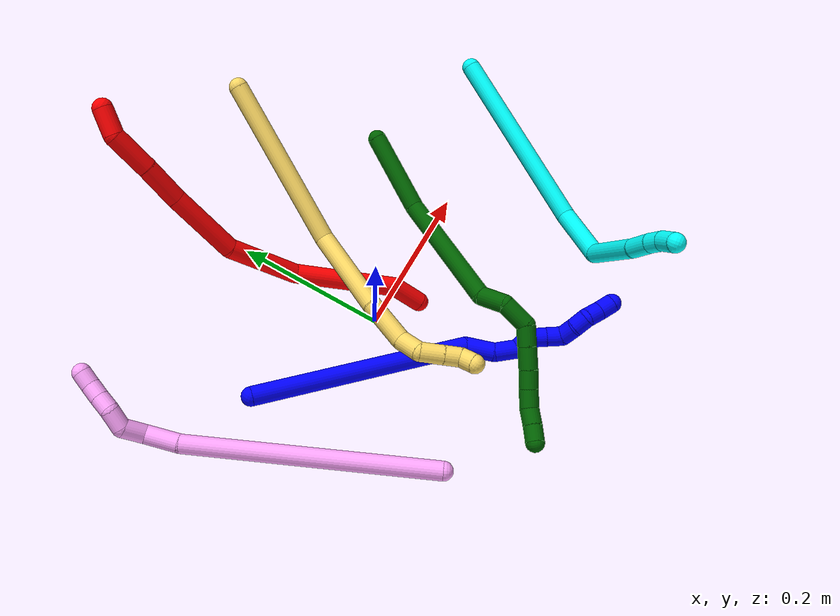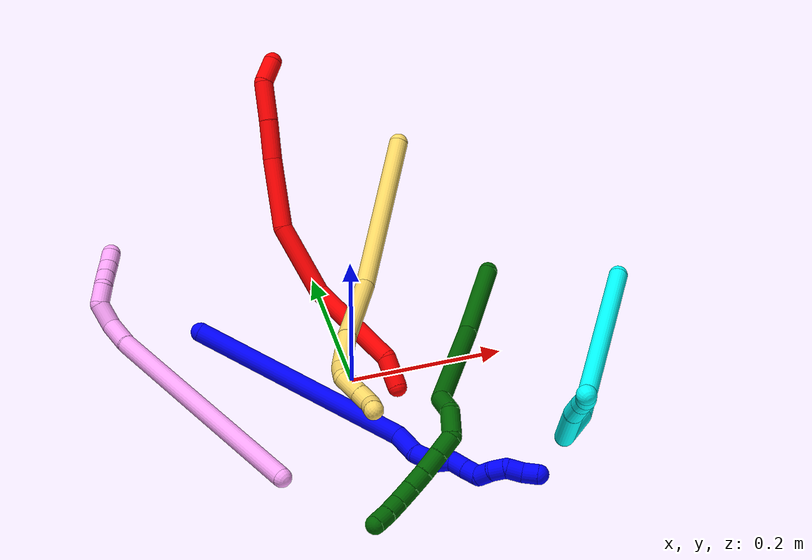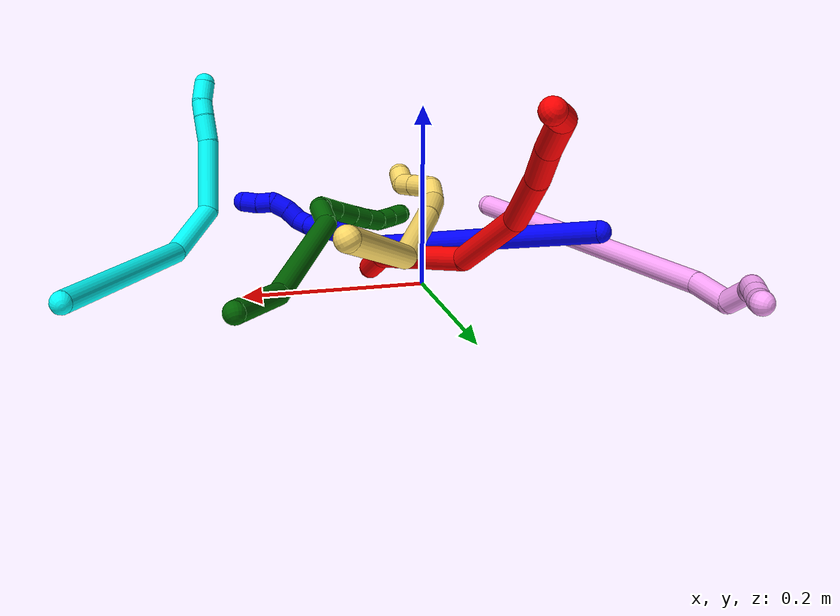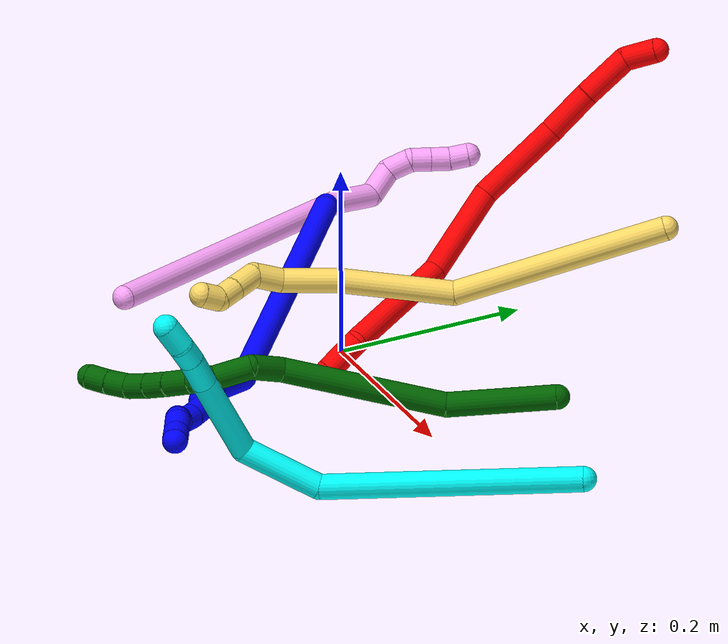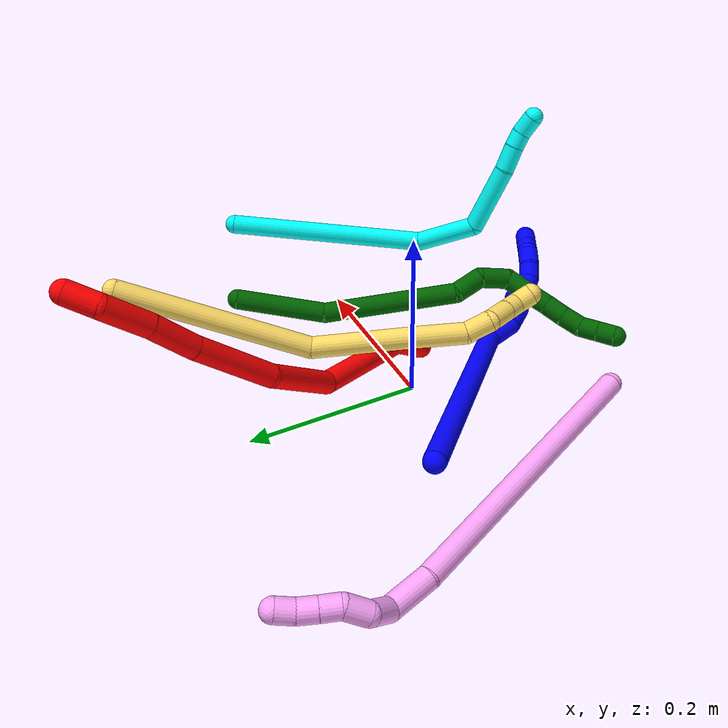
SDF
<sdf version="1.7">
 <world name="default">
  <plugin name="TubeGeneratorPlugin" filename="libtube_generator_plugin.so"/>
  <model name="photoneo_s_sensor">
   <static>1</static>
   <pose>0 0 2 1.57079 1.57079 3.14159</pose>
   <link name="link">
    <inertial><mass>0.1</mass></inertial>
    <sensor name="sensor" type="depth">
     <update_rate>30</update_rate>
     <camera>
      <horizontal_fov>1.22</horizontal_fov>
      <image><width>1920</width><height>1200</height><format>B8G8R8</format></image>
      <clip><near>0.1</near><far>4</far></clip>
      <depth_camera><output>points</output></depth_camera>
     </camera>
     <plugin name="camera_plugin" filename="libgazebo_ros_depth_camera.so">
      <baseline>0.2</baseline>
      <alwaysOn>1</alwaysOn>
      <updateRate>0.0</updateRate>
      <cameraName>camera_ir</cameraName>
      <imageTopicName>/camera/color/image_raw</imageTopicName>
      <cameraInfoTopicName>/camera/color/camera_info</cameraInfoTopicName>
      <depthImageTopicName>/camera/depth/image_raw</depthImageTopicName>
      <depthImageCameraInfoTopicName>/camera/depth/camera_info</depthImageCameraInfoTopicName>
      <pointCloudTopicName>/camera/depth/points</pointCloudTopicName>
      <frameName>fr_optical</frameName>
      <pointCloudCutoff>0.1</pointCloudCutoff>
      <pointCloudCutoffMax>2.0</pointCloudCutoffMax>
      <distortionK1>0</distortionK1>
      <distortionK2>0</distortionK2>
      <distortionK3>0</distortionK3>
      <distortionT1>0</distortionT1>
      <distortionT2>0</distortionT2>
      <CxPrime>0</CxPrime>
      <Cx>0</Cx>
      <Cy>0</Cy>
      <focalLength>0</focalLength>
      <hackBaseline>0</hackBaseline>
     </plugin>
    </sensor>
   </link>
  </model>
  <gravity>0 0 -9.8</gravity>
  <magnetic_field>6e-06 2.3e-05 -4.2e-05</magnetic_field>
  <atmosphere type="adiabatic"/>
  <physics name="default_physics" default="0" type="ode">
   <max_step_size>0.003</max_step_size>
   <real_time_factor>1</real_time_factor>
   <real_time_update_rate>1000</real_time_update_rate>
   <max_contacts>10000</max_contacts>
   <ode>
    <solver>
     <type>quick</type>
     <iters>100</iters>
     <sor>1.3</sor>
     <use_dynamic_moi_rescaling>0</use_dynamic_moi_rescaling>
    </solver>
    <constraints>
     <contact_max_correcting_vel>0</contact_max_correcting_vel>
     <contact_surface_layer>0.001</contact_surface_layer>
     <cfm>0</cfm>
     <erp>0.2</erp>
    </constraints>
   </ode>
  </physics>
  <scene><ambient>0.4 0.4 0.4 1</ambient><background>0.7 0.7 0.7 1</background><shadows>0</shadows></scene>
  <audio><device>default</device></audio>
  <spherical_coordinates>
   <surface_model>EARTH_WGS84</surface_model>
   <latitude_deg>0</latitude_deg>
   <longitude_deg>0</longitude_deg>
   <elevation>0</elevation>
   <heading_deg>0</heading_deg>
  </spherical_coordinates>
  <model name="bin">
   <static>1</static>
   <link name="bottom">
    <collision name="collision-bottom">
     <pose>0 0 -0.01 0 -0 0</pose>
     <geometry><box><size>0.8 0.6 0.02</size></box></geometry>
     <surface>
      <friction><ode><mu>100</mu><mu2>100</mu2></ode></friction>
      <contact><collide_bitmask>65535</collide_bitmask></contact>
     </surface>
    </collision>
   </link>
   <link name="west_wall">
    <collision name="collision-west_wall">
     <pose>-0.41 0 0.1 0 -0 0</pose>
     <geometry><box><size>0.02 0.6 0.2</size></box></geometry>
     <surface>
      <friction><ode><mu>100</mu><mu2>100</mu2></ode></friction>
      <contact><collide_bitmask>65535</collide_bitmask></contact>
     </surface>
    </collision>
   </link>
   <link name="east_wall">
    <collision name="collision-east_wall">
     <pose>0.41 0 0.1 0 -0 0</pose>
     <geometry><box><size>0.02 0.6 0.2</size></box></geometry>
     <surface>
      <friction><ode><mu>100</mu><mu2>100</mu2></ode></friction>
      <contact><collide_bitmask>65535</collide_bitmask></contact>
     </surface>
    </collision>
   </link>
   <link name="south_wall">
    <collision name="collision-south_wall">
     <pose>0 -0.31 0.1 0 -0 0</pose>
     <geometry><box><size>0.8 0.02 0.2</size></box></geometry>
     <surface>
      <friction><ode><mu>100</mu><mu2>100</mu2></ode></friction>
      <contact><collide_bitmask>65535</collide_bitmask></contact>
     </surface>
    </collision>
   </link>
   <link name="north_wall">
    <collision name="collision-north_wall">
     <pose>0 0.31 0.1 0 -0 0</pose>
     <geometry><box><size>0.8 0.02 0.2</size></box></geometry>
     <surface>
      <friction><ode><mu>100</mu><mu2>100</mu2></ode></friction>
      <contact><collide_bitmask>65535</collide_bitmask></contact>
     </surface>
    </collision>
   </link>
  </model>
  <model name="1">
   <static>0</static>
   <link name="1">
    <collision name="collision-cylinder-e_1_1_4">
     <pose>0.108842 -0.064272 0.068833 0.75115 0.85752 0.356648</pose>
     <geometry><cylinder><radius>0.0125</radius><length>0.287858</length></cylinder></geometry>
     <surface>
      <friction><ode><mu>1.16</mu><mu2>1.16</mu2><slip1>0</slip1><slip2>0</slip2></ode></friction>
      <contact><ode><kp>1e+06</kp><kd>1</kd><max_vel>0</max_vel><min_depth>0.001</min_depth></ode></contact>
     </surface>
    </collision>
    <visual name="visual-cylinder-e_1_1_4">
     <pose>0.108842 -0.064272 0.068833 0.75115 0.85752 0.356648</pose>
     <geometry><cylinder><radius>0.0125</radius><length>0.287858</length></cylinder></geometry>
     <material><ambient>0 0 1 1</ambient></material>
    </visual>
    <collision name="collision-cylinder-e_2_4_5">
     <pose>0.226464 -0.144867 0.142081 1.30662 0.478909 0.369485</pose>
     <geometry><cylinder><radius>0.0125</radius><length>0.038105</length></cylinder></geometry>
     <surface>
      <friction><ode><mu>1.16</mu><mu2>1.16</mu2><slip1>0</slip1><slip2>0</slip2></ode></friction>
      <contact><ode><kp>1e+06</kp><kd>1</kd><max_vel>0</max_vel><min_depth>0.001</min_depth></ode></contact>
     </surface>
    </collision>
    <visual name="visual-cylinder-e_2_4_5">
     <pose>0.226464 -0.144867 0.142081 1.30662 0.478909 0.369485</pose>
     <geometry><cylinder><radius>0.0125</radius><length>0.038105</length></cylinder></geometry>
     <material><ambient>0 0 1 1</ambient></material>
    </visual>
    <collision name="collision-cylinder-e_3_5_6">
     <pose>0.243281 -0.170931 0.154415 0.888198 0.569486 0.276749</pose>
     <geometry><cylinder><radius>0.0125</radius><length>0.029812</length></cylinder></geometry>
     <surface>
      <friction><ode><mu>1.16</mu><mu2>1.16</mu2><slip1>0</slip1><slip2>0</slip2></ode></friction>
      <contact><ode><kp>1e+06</kp><kd>1</kd><max_vel>0</max_vel><min_depth>0.001</min_depth></ode></contact>
     </surface>
    </collision>
    <visual name="visual-cylinder-e_3_5_6">
     <pose>0.243281 -0.170931 0.154415 0.888198 0.569486 0.276749</pose>
     <geometry><cylinder><radius>0.0125</radius><length>0.029812</length></cylinder></geometry>
     <material><ambient>0 0 1 1</ambient></material>
    </visual>
    <collision name="collision-cylinder-e_4_6_7">
     <pose>0.255852 -0.182697 0.171353 0.220964 0.455997 0.051469</pose>
     <geometry><cylinder><radius>0.0125</radius><length>0.020591</length></cylinder></geometry>
     <surface>
      <friction><ode><mu>1.16</mu><mu2>1.16</mu2><slip1>0</slip1><slip2>0</slip2></ode></friction>
      <contact><ode><kp>1e+06</kp><kd>1</kd><max_vel>0</max_vel><min_depth>0.001</min_depth></ode></contact>
     </surface>
    </collision>
    <visual name="visual-cylinder-e_4_6_7">
     <pose>0.255852 -0.182697 0.171353 0.220964 0.455997 0.051469</pose>
     <geometry><cylinder><radius>0.0125</radius><length>0.020591</length></cylinder></geometry>
     <material><ambient>0 0 1 1</ambient></material>
    </visual>
    <collision name="collision-cylinder-e_5_7_8">
     <pose>0.266939 -0.192554 0.185535 0.987901 0.60976 0.335717</pose>
     <geometry><cylinder><radius>0.0125</radius><length>0.022885</length></cylinder></geometry>
     <surface>
      <friction><ode><mu>1.16</mu><mu2>1.16</mu2><slip1>0</slip1><slip2>0</slip2></ode></friction>
      <contact><ode><kp>1e+06</kp><kd>1</kd><max_vel>0</max_vel><min_depth>0.001</min_depth></ode></contact>
     </surface>
    </collision>
    <visual name="visual-cylinder-e_5_7_8">
     <pose>0.266939 -0.192554 0.185535 0.987901 0.60976 0.335717</pose>
     <geometry><cylinder><radius>0.0125</radius><length>0.022885</length></cylinder></geometry>
     <material><ambient>0 0 1 1</ambient></material>
    </visual>
    <collision name="collision-cylinder-e_6_8_9">
     <pose>0.278228 -0.208187 0.195627 1.00728 0.474258 0.264789</pose>
     <geometry><cylinder><radius>0.0125</radius><length>0.020745</length></cylinder></geometry>
     <surface>
      <friction><ode><mu>1.16</mu><mu2>1.16</mu2><slip1>0</slip1><slip2>0</slip2></ode></friction>
      <contact><ode><kp>1e+06</kp><kd>1</kd><max_vel>0</max_vel><min_depth>0.001</min_depth></ode></contact>
     </surface>
    </collision>
    <visual name="visual-cylinder-e_6_8_9">
     <pose>0.278228 -0.208187 0.195627 1.00728 0.474258 0.264789</pose>
     <geometry><cylinder><radius>0.0125</radius><length>0.020745</length></cylinder></geometry>
     <material><ambient>0 0 1 1</ambient></material>
    </visual>
    <collision name="collision-cylinder-e_7_9_10">
     <pose>0.282826 -0.220637 0.209409 0.483601 -0.01387 -0.003421</pose>
     <geometry><cylinder><radius>0.0125</radius><length>0.020001</length></cylinder></geometry>
     <surface>
      <friction><ode><mu>1.16</mu><mu2>1.16</mu2><slip1>0</slip1><slip2>0</slip2></ode></friction>
      <contact><ode><kp>1e+06</kp><kd>1</kd><max_vel>0</max_vel><min_depth>0.001</min_depth></ode></contact>
     </surface>
    </collision>
    <visual name="visual-cylinder-e_7_9_10">
     <pose>0.282826 -0.220637 0.209409 0.483601 -0.01387 -0.003421</pose>
     <geometry><cylinder><radius>0.0125</radius><length>0.020001</length></cylinder></geometry>
     <material><ambient>0 0 1 1</ambient></material>
    </visual>
    <collision name="collision-cylinder-e_8_10_11">
     <pose>0.284891 -0.228873 0.227333 0.376485 0.222205 0.042498</pose>
     <geometry><cylinder><radius>0.0125</radius><length>0.02</length></cylinder></geometry>
     <surface>
      <friction><ode><mu>1.16</mu><mu2>1.16</mu2><slip1>0</slip1><slip2>0</slip2></ode></friction>
      <contact><ode><kp>1e+06</kp><kd>1</kd><max_vel>0</max_vel><min_depth>0.001</min_depth></ode></contact>
     </surface>
    </collision>
    <visual name="visual-cylinder-e_8_10_11">
     <pose>0.284891 -0.228873 0.227333 0.376485 0.222205 0.042498</pose>
     <geometry><cylinder><radius>0.0125</radius><length>0.02</length></cylinder></geometry>
     <material><ambient>0 0 1 1</ambient></material>
    </visual>
    <collision name="collision-cylinder-e_9_11_12">
     <pose>0.294439 -0.235044 0.242682 0.390711 0.824617 0.172666</pose>
     <geometry><cylinder><radius>0.0125</radius><length>0.020002</length></cylinder></geometry>
     <surface>
      <friction><ode><mu>1.16</mu><mu2>1.16</mu2><slip1>0</slip1><slip2>0</slip2></ode></friction>
      <contact><ode><kp>1e+06</kp><kd>1</kd><max_vel>0</max_vel><min_depth>0.001</min_depth></ode></contact>
     </surface>
    </collision>
    <visual name="visual-cylinder-e_9_11_12">
     <pose>0.294439 -0.235044 0.242682 0.390711 0.824617 0.172666</pose>
     <geometry><cylinder><radius>0.0125</radius><length>0.020002</length></cylinder></geometry>
     <material><ambient>0 0 1 1</ambient></material>
    </visual>
    <collision name="collision-cylinder-e_10_12_2">
     <pose>0.307498 -0.240838 0.256512 0.401579 0.608377 0.127617</pose>
     <geometry><cylinder><radius>0.0125</radius><length>0.020001</length></cylinder></geometry>
     <surface>
      <friction><ode><mu>1.16</mu><mu2>1.16</mu2><slip1>0</slip1><slip2>0</slip2></ode></friction>
      <contact><ode><kp>1e+06</kp><kd>1</kd><max_vel>0</max_vel><min_depth>0.001</min_depth></ode></contact>
     </surface>
    </collision>
    <visual name="visual-cylinder-e_10_12_2">
     <pose>0.307498 -0.240838 0.256512 0.401579 0.608377 0.127617</pose>
     <geometry><cylinder><radius>0.0125</radius><length>0.020001</length></cylinder></geometry>
     <material><ambient>0 0 1 1</ambient></material>
    </visual>
    <collision name="collision-sphere-2">
     <pose>0.313214 -0.244045 0.264066 0 -0 0</pose>
     <geometry><sphere><radius>0.0125</radius></sphere></geometry>
     <surface>
      <friction><ode><mu>1.16</mu><mu2>1.16</mu2><slip1>0</slip1><slip2>0</slip2></ode></friction>
      <contact><ode><kp>1e+06</kp><kd>1</kd><max_vel>0</max_vel><min_depth>0.001</min_depth></ode></contact>
     </surface>
    </collision>
    <visual name="visual-sphere-2">
     <pose>0.313214 -0.244045 0.264066 0 -0 0</pose>
     <geometry><sphere><radius>0.0125</radius></sphere></geometry>
     <material><ambient>0 0 1 1</ambient></material>
    </visual>
    <collision name="collision-sphere-12">
     <pose>0.301782 -0.23763 0.248959 0 -0 0</pose>
     <geometry><sphere><radius>0.0125</radius></sphere></geometry>
     <surface>
      <friction><ode><mu>1.16</mu><mu2>1.16</mu2><slip1>0</slip1><slip2>0</slip2></ode></friction>
      <contact><ode><kp>1e+06</kp><kd>1</kd><max_vel>0</max_vel><min_depth>0.001</min_depth></ode></contact>
     </surface>
    </collision>
    <visual name="visual-sphere-12">
     <pose>0.301782 -0.23763 0.248959 0 -0 0</pose>
     <geometry><sphere><radius>0.0125</radius></sphere></geometry>
     <material><ambient>0 0 1 1</ambient></material>
    </visual>
    <collision name="collision-sphere-11">
     <pose>0.287095 -0.232459 0.236404 0 -0 0</pose>
     <geometry><sphere><radius>0.0125</radius></sphere></geometry>
     <surface>
      <friction><ode><mu>1.16</mu><mu2>1.16</mu2><slip1>0</slip1><slip2>0</slip2></ode></friction>
      <contact><ode><kp>1e+06</kp><kd>1</kd><max_vel>0</max_vel><min_depth>0.001</min_depth></ode></contact>
     </surface>
    </collision>
    <visual name="visual-sphere-11">
     <pose>0.287095 -0.232459 0.236404 0 -0 0</pose>
     <geometry><sphere><radius>0.0125</radius></sphere></geometry>
     <material><ambient>0 0 1 1</ambient></material>
    </visual>
    <collision name="collision-sphere-10">
     <pose>0.282688 -0.225287 0.218262 0 -0 0</pose>
     <geometry><sphere><radius>0.0125</radius></sphere></geometry>
     <surface>
      <friction><ode><mu>1.16</mu><mu2>1.16</mu2><slip1>0</slip1><slip2>0</slip2></ode></friction>
      <contact><ode><kp>1e+06</kp><kd>1</kd><max_vel>0</max_vel><min_depth>0.001</min_depth></ode></contact>
     </surface>
    </collision>
    <visual name="visual-sphere-10">
     <pose>0.282688 -0.225287 0.218262 0 -0 0</pose>
     <geometry><sphere><radius>0.0125</radius></sphere></geometry>
     <material><ambient>0 0 1 1</ambient></material>
    </visual>
    <collision name="collision-sphere-9">
     <pose>0.282965 -0.215987 0.200556 0 -0 0</pose>
     <geometry><sphere><radius>0.0125</radius></sphere></geometry>
     <surface>
      <friction><ode><mu>1.16</mu><mu2>1.16</mu2><slip1>0</slip1><slip2>0</slip2></ode></friction>
      <contact><ode><kp>1e+06</kp><kd>1</kd><max_vel>0</max_vel><min_depth>0.001</min_depth></ode></contact>
     </surface>
    </collision>
    <visual name="visual-sphere-9">
     <pose>0.282965 -0.215987 0.200556 0 -0 0</pose>
     <geometry><sphere><radius>0.0125</radius></sphere></geometry>
     <material><ambient>0 0 1 1</ambient></material>
    </visual>
    <collision name="collision-sphere-4">
     <pose>0.217685 -0.128545 0.137666 0 -0 0</pose>
     <geometry><sphere><radius>0.0125</radius></sphere></geometry>
     <surface>
      <friction><ode><mu>1.16</mu><mu2>1.16</mu2><slip1>0</slip1><slip2>0</slip2></ode></friction>
      <contact><ode><kp>1e+06</kp><kd>1</kd><max_vel>0</max_vel><min_depth>0.001</min_depth></ode></contact>
     </surface>
    </collision>
    <visual name="visual-sphere-4">
     <pose>0.217685 -0.128545 0.137666 0 -0 0</pose>
     <geometry><sphere><radius>0.0125</radius></sphere></geometry>
     <material><ambient>0 0 1 1</ambient></material>
    </visual>
    <collision name="collision-sphere-1">
     <geometry><sphere><radius>0.0125</radius></sphere></geometry>
     <surface>
      <friction><ode><mu>1.16</mu><mu2>1.16</mu2><slip1>0</slip1><slip2>0</slip2></ode></friction>
      <contact><ode><kp>1e+06</kp><kd>1</kd><max_vel>0</max_vel><min_depth>0.001</min_depth></ode></contact>
     </surface>
    </collision>
    <visual name="visual-sphere-1">
     <geometry><sphere><radius>0.0125</radius></sphere></geometry>
     <material><ambient>0 0 1 1</ambient></material>
    </visual>
    <collision name="collision-sphere-8">
     <pose>0.273491 -0.200386 0.190698 0 -0 0</pose>
     <geometry><sphere><radius>0.0125</radius></sphere></geometry>
     <surface>
      <friction><ode><mu>1.16</mu><mu2>1.16</mu2><slip1>0</slip1><slip2>0</slip2></ode></friction>
      <contact><ode><kp>1e+06</kp><kd>1</kd><max_vel>0</max_vel><min_depth>0.001</min_depth></ode></contact>
     </surface>
    </collision>
    <visual name="visual-sphere-8">
     <pose>0.273491 -0.200386 0.190698 0 -0 0</pose>
     <geometry><sphere><radius>0.0125</radius></sphere></geometry>
     <material><ambient>0 0 1 1</ambient></material>
    </visual>
    <collision name="collision-sphere-5">
     <pose>0.235244 -0.16119 0.146496 0 -0 0</pose>
     <geometry><sphere><radius>0.0125</radius></sphere></geometry>
     <surface>
      <friction><ode><mu>1.16</mu><mu2>1.16</mu2><slip1>0</slip1><slip2>0</slip2></ode></friction>
      <contact><ode><kp>1e+06</kp><kd>1</kd><max_vel>0</max_vel><min_depth>0.001</min_depth></ode></contact>
     </surface>
    </collision>
    <visual name="visual-sphere-5">
     <pose>0.235244 -0.16119 0.146496 0 -0 0</pose>
     <geometry><sphere><radius>0.0125</radius></sphere></geometry>
     <material><ambient>0 0 1 1</ambient></material>
    </visual>
    <collision name="collision-sphere-6">
     <pose>0.251318 -0.180671 0.162334 0 -0 0</pose>
     <geometry><sphere><radius>0.0125</radius></sphere></geometry>
     <surface>
      <friction><ode><mu>1.16</mu><mu2>1.16</mu2><slip1>0</slip1><slip2>0</slip2></ode></friction>
      <contact><ode><kp>1e+06</kp><kd>1</kd><max_vel>0</max_vel><min_depth>0.001</min_depth></ode></contact>
     </surface>
    </collision>
    <visual name="visual-sphere-6">
     <pose>0.251318 -0.180671 0.162334 0 -0 0</pose>
     <geometry><sphere><radius>0.0125</radius></sphere></geometry>
     <material><ambient>0 0 1 1</ambient></material>
    </visual>
    <collision name="collision-sphere-7">
     <pose>0.260386 -0.184723 0.180372 0 -0 0</pose>
     <geometry><sphere><radius>0.0125</radius></sphere></geometry>
     <surface>
      <friction><ode><mu>1.16</mu><mu2>1.16</mu2><slip1>0</slip1><slip2>0</slip2></ode></friction>
      <contact><ode><kp>1e+06</kp><kd>1</kd><max_vel>0</max_vel><min_depth>0.001</min_depth></ode></contact>
     </surface>
    </collision>
    <visual name="visual-sphere-7">
     <pose>0.260386 -0.184723 0.180372 0 -0 0</pose>
     <geometry><sphere><radius>0.0125</radius></sphere></geometry>
     <material><ambient>0 0 1 1</ambient></material>
    </visual>
    <inertial>
     <pose>0.175513 -0.120227 0.120767 0 -0 0</pose>
     <mass>0.5</mass>
     <inertia>
      <ixx>0.001728</ixx>
      <ixy>0</ixy>
      <ixz>0</ixz>
      <iyy>0.002185</iyy>
      <iyz>0</iyz>
      <izz>-0.000595</izz>
     </inertia>
    </inertial>
   </link>
   <pose>-0.179378 0.071889 0.066837 -0.53611 0.897169 -0.610195</pose>
  </model>
  <model name="2">
   <static>0</static>
   <link name="2">
    <collision name="collision-cylinder-e_1_1_4">
     <pose>-0.001969 0.001072 0.020242 -0.052922 -0.096819 0.002565</pose>
     <geometry><cylinder><radius>0.0125</radius><length>0.040732</length></cylinder></geometry>
     <surface>
      <friction><ode><mu>1.16</mu><mu2>1.16</mu2><slip1>0</slip1><slip2>0</slip2></ode></friction>
      <contact><ode><kp>1e+06</kp><kd>1</kd><max_vel>0</max_vel><min_depth>0.001</min_depth></ode></contact>
     </surface>
    </collision>
    <visual name="visual-cylinder-e_1_1_4">
     <pose>-0.001969 0.001072 0.020242 -0.052922 -0.096819 0.002565</pose>
     <geometry><cylinder><radius>0.0125</radius><length>0.040732</length></cylinder></geometry>
     <material><ambient>1 0 0 1</ambient></material>
    </visual>
    <collision name="collision-cylinder-e_2_4_5">
     <pose>-0.007647 0.035342 0.097527 -0.527059 -0.056149 0.015153</pose>
     <geometry><cylinder><radius>0.0125</radius><length>0.132208</length></cylinder></geometry>
     <surface>
      <friction><ode><mu>1.16</mu><mu2>1.16</mu2><slip1>0</slip1><slip2>0</slip2></ode></friction>
      <contact><ode><kp>1e+06</kp><kd>1</kd><max_vel>0</max_vel><min_depth>0.001</min_depth></ode></contact>
     </surface>
    </collision>
    <visual name="visual-cylinder-e_2_4_5">
     <pose>-0.007647 0.035342 0.097527 -0.527059 -0.056149 0.015153</pose>
     <geometry><cylinder><radius>0.0125</radius><length>0.132208</length></cylinder></geometry>
     <material><ambient>1 0 0 1</ambient></material>
    </visual>
    <collision name="collision-cylinder-e_3_5_6">
     <pose>-0.024921 0.074855 0.200776 -0.135835 -0.283055 0.019383</pose>
     <geometry><cylinder><radius>0.0125</radius><length>0.097135</length></cylinder></geometry>
     <surface>
      <friction><ode><mu>1.16</mu><mu2>1.16</mu2><slip1>0</slip1><slip2>0</slip2></ode></friction>
      <contact><ode><kp>1e+06</kp><kd>1</kd><max_vel>0</max_vel><min_depth>0.001</min_depth></ode></contact>
     </surface>
    </collision>
    <visual name="visual-cylinder-e_3_5_6">
     <pose>-0.024921 0.074855 0.200776 -0.135835 -0.283055 0.019383</pose>
     <geometry><cylinder><radius>0.0125</radius><length>0.097135</length></cylinder></geometry>
     <material><ambient>1 0 0 1</ambient></material>
    </visual>
    <collision name="collision-cylinder-e_4_6_7">
     <pose>-0.040608 0.074345 0.292365 0.149274 -0.046213 -0.003456</pose>
     <geometry><cylinder><radius>0.0125</radius><length>0.091886</length></cylinder></geometry>
     <surface>
      <friction><ode><mu>1.16</mu><mu2>1.16</mu2><slip1>0</slip1><slip2>0</slip2></ode></friction>
      <contact><ode><kp>1e+06</kp><kd>1</kd><max_vel>0</max_vel><min_depth>0.001</min_depth></ode></contact>
     </surface>
    </collision>
    <visual name="visual-cylinder-e_4_6_7">
     <pose>-0.040608 0.074345 0.292365 0.149274 -0.046213 -0.003456</pose>
     <geometry><cylinder><radius>0.0125</radius><length>0.091886</length></cylinder></geometry>
     <material><ambient>1 0 0 1</ambient></material>
    </visual>
    <collision name="collision-cylinder-e_5_7_8">
     <pose>-0.044849 0.061682 0.362741 0.229475 -0.082348 -0.009495</pose>
     <geometry><cylinder><radius>0.0125</radius><length>0.051505</length></cylinder></geometry>
     <surface>
      <friction><ode><mu>1.16</mu><mu2>1.16</mu2><slip1>0</slip1><slip2>0</slip2></ode></friction>
      <contact><ode><kp>1e+06</kp><kd>1</kd><max_vel>0</max_vel><min_depth>0.001</min_depth></ode></contact>
     </surface>
    </collision>
    <visual name="visual-cylinder-e_5_7_8">
     <pose>-0.044849 0.061682 0.362741 0.229475 -0.082348 -0.009495</pose>
     <geometry><cylinder><radius>0.0125</radius><length>0.051505</length></cylinder></geometry>
     <material><ambient>1 0 0 1</ambient></material>
    </visual>
    <collision name="collision-cylinder-e_6_8_9">
     <pose>-0.047849 0.051544 0.413618 0.164618 -0.033608 -0.002773</pose>
     <geometry><cylinder><radius>0.0125</radius><length>0.052508</length></cylinder></geometry>
     <surface>
      <friction><ode><mu>1.16</mu><mu2>1.16</mu2><slip1>0</slip1><slip2>0</slip2></ode></friction>
      <contact><ode><kp>1e+06</kp><kd>1</kd><max_vel>0</max_vel><min_depth>0.001</min_depth></ode></contact>
     </surface>
    </collision>
    <visual name="visual-cylinder-e_6_8_9">
     <pose>-0.047849 0.051544 0.413618 0.164618 -0.033608 -0.002773</pose>
     <geometry><cylinder><radius>0.0125</radius><length>0.052508</length></cylinder></geometry>
     <material><ambient>1 0 0 1</ambient></material>
    </visual>
    <collision name="collision-cylinder-e_7_9_2">
     <pose>-0.04131 0.040913 0.453441 0.426304 0.451422 0.099318</pose>
     <geometry><cylinder><radius>0.0125</radius><length>0.034026</length></cylinder></geometry>
     <surface>
      <friction><ode><mu>1.16</mu><mu2>1.16</mu2><slip1>0</slip1><slip2>0</slip2></ode></friction>
      <contact><ode><kp>1e+06</kp><kd>1</kd><max_vel>0</max_vel><min_depth>0.001</min_depth></ode></contact>
     </surface>
    </collision>
    <visual name="visual-cylinder-e_7_9_2">
     <pose>-0.04131 0.040913 0.453441 0.426304 0.451422 0.099318</pose>
     <geometry><cylinder><radius>0.0125</radius><length>0.034026</length></cylinder></geometry>
     <material><ambient>1 0 0 1</ambient></material>
    </visual>
    <collision name="collision-sphere-2">
     <pose>-0.033888 0.034583 0.467379 0 -0 0</pose>
     <geometry><sphere><radius>0.0125</radius></sphere></geometry>
     <surface>
      <friction><ode><mu>1.16</mu><mu2>1.16</mu2><slip1>0</slip1><slip2>0</slip2></ode></friction>
      <contact><ode><kp>1e+06</kp><kd>1</kd><max_vel>0</max_vel><min_depth>0.001</min_depth></ode></contact>
     </surface>
    </collision>
    <visual name="visual-sphere-2">
     <pose>-0.033888 0.034583 0.467379 0 -0 0</pose>
     <geometry><sphere><radius>0.0125</radius></sphere></geometry>
     <material><ambient>1 0 0 1</ambient></material>
    </visual>
    <collision name="collision-sphere-9">
     <pose>-0.048732 0.047244 0.439502 0 -0 0</pose>
     <geometry><sphere><radius>0.0125</radius></sphere></geometry>
     <surface>
      <friction><ode><mu>1.16</mu><mu2>1.16</mu2><slip1>0</slip1><slip2>0</slip2></ode></friction>
      <contact><ode><kp>1e+06</kp><kd>1</kd><max_vel>0</max_vel><min_depth>0.001</min_depth></ode></contact>
     </surface>
    </collision>
    <visual name="visual-sphere-9">
     <pose>-0.048732 0.047244 0.439502 0 -0 0</pose>
     <geometry><sphere><radius>0.0125</radius></sphere></geometry>
     <material><ambient>1 0 0 1</ambient></material>
    </visual>
    <collision name="collision-sphere-4">
     <pose>-0.003937 0.002145 0.040484 0 -0 0</pose>
     <geometry><sphere><radius>0.0125</radius></sphere></geometry>
     <surface>
      <friction><ode><mu>1.16</mu><mu2>1.16</mu2><slip1>0</slip1><slip2>0</slip2></ode></friction>
      <contact><ode><kp>1e+06</kp><kd>1</kd><max_vel>0</max_vel><min_depth>0.001</min_depth></ode></contact>
     </surface>
    </collision>
    <visual name="visual-sphere-4">
     <pose>-0.003937 0.002145 0.040484 0 -0 0</pose>
     <geometry><sphere><radius>0.0125</radius></sphere></geometry>
     <material><ambient>1 0 0 1</ambient></material>
    </visual>
    <collision name="collision-sphere-1">
     <geometry><sphere><radius>0.0125</radius></sphere></geometry>
     <surface>
      <friction><ode><mu>1.16</mu><mu2>1.16</mu2><slip1>0</slip1><slip2>0</slip2></ode></friction>
      <contact><ode><kp>1e+06</kp><kd>1</kd><max_vel>0</max_vel><min_depth>0.001</min_depth></ode></contact>
     </surface>
    </collision>
    <visual name="visual-sphere-1">
     <geometry><sphere><radius>0.0125</radius></sphere></geometry>
     <material><ambient>1 0 0 1</ambient></material>
    </visual>
    <collision name="collision-sphere-8">
     <pose>-0.046967 0.055844 0.387733 0 -0 0</pose>
     <geometry><sphere><radius>0.0125</radius></sphere></geometry>
     <surface>
      <friction><ode><mu>1.16</mu><mu2>1.16</mu2><slip1>0</slip1><slip2>0</slip2></ode></friction>
      <contact><ode><kp>1e+06</kp><kd>1</kd><max_vel>0</max_vel><min_depth>0.001</min_depth></ode></contact>
     </surface>
    </collision>
    <visual name="visual-sphere-8">
     <pose>-0.046967 0.055844 0.387733 0 -0 0</pose>
     <geometry><sphere><radius>0.0125</radius></sphere></geometry>
     <material><ambient>1 0 0 1</ambient></material>
    </visual>
    <collision name="collision-sphere-5">
     <pose>-0.011357 0.06854 0.15457 0 -0 0</pose>
     <geometry><sphere><radius>0.0125</radius></sphere></geometry>
     <surface>
      <friction><ode><mu>1.16</mu><mu2>1.16</mu2><slip1>0</slip1><slip2>0</slip2></ode></friction>
      <contact><ode><kp>1e+06</kp><kd>1</kd><max_vel>0</max_vel><min_depth>0.001</min_depth></ode></contact>
     </surface>
    </collision>
    <visual name="visual-sphere-5">
     <pose>-0.011357 0.06854 0.15457 0 -0 0</pose>
     <geometry><sphere><radius>0.0125</radius></sphere></geometry>
     <material><ambient>1 0 0 1</ambient></material>
    </visual>
    <collision name="collision-sphere-6">
     <pose>-0.038486 0.08117 0.246981 0 -0 0</pose>
     <geometry><sphere><radius>0.0125</radius></sphere></geometry>
     <surface>
      <friction><ode><mu>1.16</mu><mu2>1.16</mu2><slip1>0</slip1><slip2>0</slip2></ode></friction>
      <contact><ode><kp>1e+06</kp><kd>1</kd><max_vel>0</max_vel><min_depth>0.001</min_depth></ode></contact>
     </surface>
    </collision>
    <visual name="visual-sphere-6">
     <pose>-0.038486 0.08117 0.246981 0 -0 0</pose>
     <geometry><sphere><radius>0.0125</radius></sphere></geometry>
     <material><ambient>1 0 0 1</ambient></material>
    </visual>
    <collision name="collision-sphere-7">
     <pose>-0.042731 0.06752 0.337748 0 -0 0</pose>
     <geometry><sphere><radius>0.0125</radius></sphere></geometry>
     <surface>
      <friction><ode><mu>1.16</mu><mu2>1.16</mu2><slip1>0</slip1><slip2>0</slip2></ode></friction>
      <contact><ode><kp>1e+06</kp><kd>1</kd><max_vel>0</max_vel><min_depth>0.001</min_depth></ode></contact>
     </surface>
    </collision>
    <visual name="visual-sphere-7">
     <pose>-0.042731 0.06752 0.337748 0 -0 0</pose>
     <geometry><sphere><radius>0.0125</radius></sphere></geometry>
     <material><ambient>1 0 0 1</ambient></material>
    </visual>
    <inertial>
     <pose>-0.026943 0.052188 0.23183 0 -0 0</pose>
     <mass>0.5</mass>
     <inertia>
      <ixx>0.000383</ixx>
      <ixy>0</ixy>
      <ixz>0</ixz>
      <iyy>0.000364</iyy>
      <iyz>0</iyz>
      <izz>-1.9e-05</izz>
     </inertia>
    </inertial>
   </link>
   <pose>0.049711 -0.038583 0.011495 -0.833841 0.696715 0.549936</pose>
  </model>
  <model name="3">
   <static>0</static>
   <link name="3">
    <collision name="collision-cylinder-e_1_1_4">
     <pose>-0.059595 -0.046263 -0.102032 2.7159 -0.488881 -1.71365</pose>
     <geometry><cylinder><radius>0.0125</radius><length>0.253789</length></cylinder></geometry>
     <surface>
      <friction><ode><mu>1.16</mu><mu2>1.16</mu2><slip1>0</slip1><slip2>0</slip2></ode></friction>
      <contact><ode><kp>1e+06</kp><kd>1</kd><max_vel>0</max_vel><min_depth>0.001</min_depth></ode></contact>
     </surface>
    </collision>
    <visual name="visual-cylinder-e_1_1_4">
     <pose>-0.059595 -0.046263 -0.102032 2.7159 -0.488881 -1.71365</pose>
     <geometry><cylinder><radius>0.0125</radius><length>0.253789</length></cylinder></geometry>
     <material><ambient>0.003922 1 0.996078 1</ambient></material>
    </visual>
    <collision name="collision-cylinder-e_2_4_5">
     <pose>-0.122996 -0.120224 -0.233208 2.38162 -0.094412 -0.235467</pose>
     <geometry><cylinder><radius>0.0125</radius><length>0.080774</length></cylinder></geometry>
     <surface>
      <friction><ode><mu>1.16</mu><mu2>1.16</mu2><slip1>0</slip1><slip2>0</slip2></ode></friction>
      <contact><ode><kp>1e+06</kp><kd>1</kd><max_vel>0</max_vel><min_depth>0.001</min_depth></ode></contact>
     </surface>
    </collision>
    <visual name="visual-cylinder-e_2_4_5">
     <pose>-0.122996 -0.120224 -0.233208 2.38162 -0.094412 -0.235467</pose>
     <geometry><cylinder><radius>0.0125</radius><length>0.080774</length></cylinder></geometry>
     <material><ambient>0.003922 1 0.996078 1</ambient></material>
    </visual>
    <collision name="collision-cylinder-e_3_5_6">
     <pose>-0.099614 -0.173279 -0.285434 2.30929 0.670443 1.33504</pose>
     <geometry><cylinder><radius>0.0125</radius><length>0.08752</length></cylinder></geometry>
     <surface>
      <friction><ode><mu>1.16</mu><mu2>1.16</mu2><slip1>0</slip1><slip2>0</slip2></ode></friction>
      <contact><ode><kp>1e+06</kp><kd>1</kd><max_vel>0</max_vel><min_depth>0.001</min_depth></ode></contact>
     </surface>
    </collision>
    <visual name="visual-cylinder-e_3_5_6">
     <pose>-0.099614 -0.173279 -0.285434 2.30929 0.670443 1.33504</pose>
     <geometry><cylinder><radius>0.0125</radius><length>0.08752</length></cylinder></geometry>
     <material><ambient>0.003922 1 0.996078 1</ambient></material>
    </visual>
    <collision name="collision-cylinder-e_4_6_7">
     <pose>-0.061054 -0.205956 -0.317402 2.45244 0.779131 1.70486</pose>
     <geometry><cylinder><radius>0.0125</radius><length>0.032365</length></cylinder></geometry>
     <surface>
      <friction><ode><mu>1.16</mu><mu2>1.16</mu2><slip1>0</slip1><slip2>0</slip2></ode></friction>
      <contact><ode><kp>1e+06</kp><kd>1</kd><max_vel>0</max_vel><min_depth>0.001</min_depth></ode></contact>
     </surface>
    </collision>
    <visual name="visual-cylinder-e_4_6_7">
     <pose>-0.061054 -0.205956 -0.317402 2.45244 0.779131 1.70486</pose>
     <geometry><cylinder><radius>0.0125</radius><length>0.032365</length></cylinder></geometry>
     <material><ambient>0.003922 1 0.996078 1</ambient></material>
    </visual>
    <collision name="collision-cylinder-e_5_7_8">
     <pose>-0.043143 -0.217852 -0.332496 2.50649 0.703371 1.68071</pose>
     <geometry><cylinder><radius>0.0125</radius><length>0.020223</length></cylinder></geometry>
     <surface>
      <friction><ode><mu>1.16</mu><mu2>1.16</mu2><slip1>0</slip1><slip2>0</slip2></ode></friction>
      <contact><ode><kp>1e+06</kp><kd>1</kd><max_vel>0</max_vel><min_depth>0.001</min_depth></ode></contact>
     </surface>
    </collision>
    <visual name="visual-cylinder-e_5_7_8">
     <pose>-0.043143 -0.217852 -0.332496 2.50649 0.703371 1.68071</pose>
     <geometry><cylinder><radius>0.0125</radius><length>0.020223</length></cylinder></geometry>
     <material><ambient>0.003922 1 0.996078 1</ambient></material>
    </visual>
    <collision name="collision-cylinder-e_6_8_2">
     <pose>-0.030481 -0.230678 -0.346109 2.30222 0.504585 1.04778</pose>
     <geometry><cylinder><radius>0.0125</radius><length>0.02533</length></cylinder></geometry>
     <surface>
      <friction><ode><mu>1.16</mu><mu2>1.16</mu2><slip1>0</slip1><slip2>0</slip2></ode></friction>
      <contact><ode><kp>1e+06</kp><kd>1</kd><max_vel>0</max_vel><min_depth>0.001</min_depth></ode></contact>
     </surface>
    </collision>
    <visual name="visual-cylinder-e_6_8_2">
     <pose>-0.030481 -0.230678 -0.346109 2.30222 0.504585 1.04778</pose>
     <geometry><cylinder><radius>0.0125</radius><length>0.02533</length></cylinder></geometry>
     <material><ambient>0.003922 1 0.996078 1</ambient></material>
    </visual>
    <collision name="collision-sphere-2">
     <pose>-0.024358 -0.238929 -0.353514 0 -0 0</pose>
     <geometry><sphere><radius>0.0125</radius></sphere></geometry>
     <surface>
      <friction><ode><mu>1.16</mu><mu2>1.16</mu2><slip1>0</slip1><slip2>0</slip2></ode></friction>
      <contact><ode><kp>1e+06</kp><kd>1</kd><max_vel>0</max_vel><min_depth>0.001</min_depth></ode></contact>
     </surface>
    </collision>
    <visual name="visual-sphere-2">
     <pose>-0.024358 -0.238929 -0.353514 0 -0 0</pose>
     <geometry><sphere><radius>0.0125</radius></sphere></geometry>
     <material><ambient>0.003922 1 0.996078 1</ambient></material>
    </visual>
    <collision name="collision-sphere-4">
     <pose>-0.119189 -0.092525 -0.204063 0 -0 0</pose>
     <geometry><sphere><radius>0.0125</radius></sphere></geometry>
     <surface>
      <friction><ode><mu>1.16</mu><mu2>1.16</mu2><slip1>0</slip1><slip2>0</slip2></ode></friction>
      <contact><ode><kp>1e+06</kp><kd>1</kd><max_vel>0</max_vel><min_depth>0.001</min_depth></ode></contact>
     </surface>
    </collision>
    <visual name="visual-sphere-4">
     <pose>-0.119189 -0.092525 -0.204063 0 -0 0</pose>
     <geometry><sphere><radius>0.0125</radius></sphere></geometry>
     <material><ambient>0.003922 1 0.996078 1</ambient></material>
    </visual>
    <collision name="collision-sphere-1">
     <geometry><sphere><radius>0.0125</radius></sphere></geometry>
     <surface>
      <friction><ode><mu>1.16</mu><mu2>1.16</mu2><slip1>0</slip1><slip2>0</slip2></ode></friction>
      <contact><ode><kp>1e+06</kp><kd>1</kd><max_vel>0</max_vel><min_depth>0.001</min_depth></ode></contact>
     </surface>
    </collision>
    <visual name="visual-sphere-1">
     <geometry><sphere><radius>0.0125</radius></sphere></geometry>
     <material><ambient>0.003922 1 0.996078 1</ambient></material>
    </visual>
    <collision name="collision-sphere-8">
     <pose>-0.036604 -0.222427 -0.338704 0 -0 0</pose>
     <geometry><sphere><radius>0.0125</radius></sphere></geometry>
     <surface>
      <friction><ode><mu>1.16</mu><mu2>1.16</mu2><slip1>0</slip1><slip2>0</slip2></ode></friction>
      <contact><ode><kp>1e+06</kp><kd>1</kd><max_vel>0</max_vel><min_depth>0.001</min_depth></ode></contact>
     </surface>
    </collision>
    <visual name="visual-sphere-8">
     <pose>-0.036604 -0.222427 -0.338704 0 -0 0</pose>
     <geometry><sphere><radius>0.0125</radius></sphere></geometry>
     <material><ambient>0.003922 1 0.996078 1</ambient></material>
    </visual>
    <collision name="collision-sphere-5">
     <pose>-0.126804 -0.147923 -0.262352 0 -0 0</pose>
     <geometry><sphere><radius>0.0125</radius></sphere></geometry>
     <surface>
      <friction><ode><mu>1.16</mu><mu2>1.16</mu2><slip1>0</slip1><slip2>0</slip2></ode></friction>
      <contact><ode><kp>1e+06</kp><kd>1</kd><max_vel>0</max_vel><min_depth>0.001</min_depth></ode></contact>
     </surface>
    </collision>
    <visual name="visual-sphere-5">
     <pose>-0.126804 -0.147923 -0.262352 0 -0 0</pose>
     <geometry><sphere><radius>0.0125</radius></sphere></geometry>
     <material><ambient>0.003922 1 0.996078 1</ambient></material>
    </visual>
    <collision name="collision-sphere-6">
     <pose>-0.072425 -0.198634 -0.308515 0 -0 0</pose>
     <geometry><sphere><radius>0.0125</radius></sphere></geometry>
     <surface>
      <friction><ode><mu>1.16</mu><mu2>1.16</mu2><slip1>0</slip1><slip2>0</slip2></ode></friction>
      <contact><ode><kp>1e+06</kp><kd>1</kd><max_vel>0</max_vel><min_depth>0.001</min_depth></ode></contact>
     </surface>
    </collision>
    <visual name="visual-sphere-6">
     <pose>-0.072425 -0.198634 -0.308515 0 -0 0</pose>
     <geometry><sphere><radius>0.0125</radius></sphere></geometry>
     <material><ambient>0.003922 1 0.996078 1</ambient></material>
    </visual>
    <collision name="collision-sphere-7">
     <pose>-0.049683 -0.213277 -0.326288 0 -0 0</pose>
     <geometry><sphere><radius>0.0125</radius></sphere></geometry>
     <surface>
      <friction><ode><mu>1.16</mu><mu2>1.16</mu2><slip1>0</slip1><slip2>0</slip2></ode></friction>
      <contact><ode><kp>1e+06</kp><kd>1</kd><max_vel>0</max_vel><min_depth>0.001</min_depth></ode></contact>
     </surface>
    </collision>
    <visual name="visual-sphere-7">
     <pose>-0.049683 -0.213277 -0.326288 0 -0 0</pose>
     <geometry><sphere><radius>0.0125</radius></sphere></geometry>
     <material><ambient>0.003922 1 0.996078 1</ambient></material>
    </visual>
    <inertial>
     <pose>-0.074796 -0.107063 -0.190952 0 -0 0</pose>
     <mass>0.5</mass>
     <inertia>
      <ixx>-0.001276</ixx>
      <ixy>0</ixy>
      <ixz>0</ixz>
      <iyy>-0.000749</iyy>
      <iyz>0</iyz>
      <izz>0.00115</izz>
     </inertia>
    </inertial>
   </link>
   <pose>0.387648 0.066266 0.030201 -1.7676 -0.937166 0.232244</pose>
  </model>
  <model name="4">
   <static>0</static>
   <link name="4">
    <collision name="collision-cylinder-e_1_1_4">
     <pose>-0.003031 0.005099 0.165273 -0.030845 -0.01833 0.000283</pose>
     <geometry><cylinder><radius>0.0125</radius><length>0.330759</length></cylinder></geometry>
     <surface>
      <friction><ode><mu>1.16</mu><mu2>1.16</mu2><slip1>0</slip1><slip2>0</slip2></ode></friction>
      <contact><ode><kp>1e+06</kp><kd>1</kd><max_vel>0</max_vel><min_depth>0.001</min_depth></ode></contact>
     </surface>
    </collision>
    <visual name="visual-cylinder-e_1_1_4">
     <pose>-0.003031 0.005099 0.165273 -0.030845 -0.01833 0.000283</pose>
     <geometry><cylinder><radius>0.0125</radius><length>0.330759</length></cylinder></geometry>
     <material><ambient>1 0.65098 0.996078 1</ambient></material>
    </visual>
    <collision name="collision-cylinder-e_2_4_5">
     <pose>-0.009453 0.014752 0.354209 -0.190096 -0.139786 0.013348</pose>
     <geometry><cylinder><radius>0.0125</radius><length>0.048668</length></cylinder></geometry>
     <surface>
      <friction><ode><mu>1.16</mu><mu2>1.16</mu2><slip1>0</slip1><slip2>0</slip2></ode></friction>
      <contact><ode><kp>1e+06</kp><kd>1</kd><max_vel>0</max_vel><min_depth>0.001</min_depth></ode></contact>
     </surface>
    </collision>
    <visual name="visual-cylinder-e_2_4_5">
     <pose>-0.009453 0.014752 0.354209 -0.190096 -0.139786 0.013348</pose>
     <geometry><cylinder><radius>0.0125</radius><length>0.048668</length></cylinder></geometry>
     <material><ambient>1 0.65098 0.996078 1</ambient></material>
    </visual>
    <collision name="collision-cylinder-e_3_5_6">
     <pose>-0.003034 0.021844 0.390733 -0.19486 0.642395 -0.065017</pose>
     <geometry><cylinder><radius>0.0125</radius><length>0.032747</length></cylinder></geometry>
     <surface>
      <friction><ode><mu>1.16</mu><mu2>1.16</mu2><slip1>0</slip1><slip2>0</slip2></ode></friction>
      <contact><ode><kp>1e+06</kp><kd>1</kd><max_vel>0</max_vel><min_depth>0.001</min_depth></ode></contact>
     </surface>
    </collision>
    <visual name="visual-cylinder-e_3_5_6">
     <pose>-0.003034 0.021844 0.390733 -0.19486 0.642395 -0.065017</pose>
     <geometry><cylinder><radius>0.0125</radius><length>0.032747</length></cylinder></geometry>
     <material><ambient>1 0.65098 0.996078 1</ambient></material>
    </visual>
    <collision name="collision-cylinder-e_4_6_7">
     <pose>0.011464 0.034381 0.410767 -0.948496 0.364015 -0.188388</pose>
     <geometry><cylinder><radius>0.0125</radius><length>0.026336</length></cylinder></geometry>
     <surface>
      <friction><ode><mu>1.16</mu><mu2>1.16</mu2><slip1>0</slip1><slip2>0</slip2></ode></friction>
      <contact><ode><kp>1e+06</kp><kd>1</kd><max_vel>0</max_vel><min_depth>0.001</min_depth></ode></contact>
     </surface>
    </collision>
    <visual name="visual-cylinder-e_4_6_7">
     <pose>0.011464 0.034381 0.410767 -0.948496 0.364015 -0.188388</pose>
     <geometry><cylinder><radius>0.0125</radius><length>0.026336</length></cylinder></geometry>
     <material><ambient>1 0.65098 0.996078 1</ambient></material>
    </visual>
    <collision name="collision-cylinder-e_5_7_8">
     <pose>0.014977 0.0516 0.425335 -0.773498 -0.113235 0.046157</pose>
     <geometry><cylinder><radius>0.0125</radius><length>0.020803</length></cylinder></geometry>
     <surface>
      <friction><ode><mu>1.16</mu><mu2>1.16</mu2><slip1>0</slip1><slip2>0</slip2></ode></friction>
      <contact><ode><kp>1e+06</kp><kd>1</kd><max_vel>0</max_vel><min_depth>0.001</min_depth></ode></contact>
     </surface>
    </collision>
    <visual name="visual-cylinder-e_5_7_8">
     <pose>0.014977 0.0516 0.425335 -0.773498 -0.113235 0.046157</pose>
     <geometry><cylinder><radius>0.0125</radius><length>0.020803</length></cylinder></geometry>
     <material><ambient>1 0.65098 0.996078 1</ambient></material>
    </visual>
    <collision name="collision-cylinder-e_6_8_9">
     <pose>0.012726 0.066201 0.439787 -0.807798 -0.104891 0.044864</pose>
     <geometry><cylinder><radius>0.0125</radius><length>0.020538</length></cylinder></geometry>
     <surface>
      <friction><ode><mu>1.16</mu><mu2>1.16</mu2><slip1>0</slip1><slip2>0</slip2></ode></friction>
      <contact><ode><kp>1e+06</kp><kd>1</kd><max_vel>0</max_vel><min_depth>0.001</min_depth></ode></contact>
     </surface>
    </collision>
    <visual name="visual-cylinder-e_6_8_9">
     <pose>0.012726 0.066201 0.439787 -0.807798 -0.104891 0.044864</pose>
     <geometry><cylinder><radius>0.0125</radius><length>0.020538</length></cylinder></geometry>
     <material><ambient>1 0.65098 0.996078 1</ambient></material>
    </visual>
    <collision name="collision-cylinder-e_7_9_2">
     <pose>0.012643 0.08121 0.45335 -0.86461 0.098615 -0.045531</pose>
     <geometry><cylinder><radius>0.0125</radius><length>0.020148</length></cylinder></geometry>
     <surface>
      <friction><ode><mu>1.16</mu><mu2>1.16</mu2><slip1>0</slip1><slip2>0</slip2></ode></friction>
      <contact><ode><kp>1e+06</kp><kd>1</kd><max_vel>0</max_vel><min_depth>0.001</min_depth></ode></contact>
     </surface>
    </collision>
    <visual name="visual-cylinder-e_7_9_2">
     <pose>0.012643 0.08121 0.45335 -0.86461 0.098615 -0.045531</pose>
     <geometry><cylinder><radius>0.0125</radius><length>0.020148</length></cylinder></geometry>
     <material><ambient>1 0.65098 0.996078 1</ambient></material>
    </visual>
    <collision name="collision-sphere-2">
     <pose>0.013635 0.088838 0.459856 0 -0 0</pose>
     <geometry><sphere><radius>0.0125</radius></sphere></geometry>
     <surface>
      <friction><ode><mu>1.16</mu><mu2>1.16</mu2><slip1>0</slip1><slip2>0</slip2></ode></friction>
      <contact><ode><kp>1e+06</kp><kd>1</kd><max_vel>0</max_vel><min_depth>0.001</min_depth></ode></contact>
     </surface>
    </collision>
    <visual name="visual-sphere-2">
     <pose>0.013635 0.088838 0.459856 0 -0 0</pose>
     <geometry><sphere><radius>0.0125</radius></sphere></geometry>
     <material><ambient>1 0.65098 0.996078 1</ambient></material>
    </visual>
    <collision name="collision-sphere-9">
     <pose>0.011651 0.073583 0.446845 0 -0 0</pose>
     <geometry><sphere><radius>0.0125</radius></sphere></geometry>
     <surface>
      <friction><ode><mu>1.16</mu><mu2>1.16</mu2><slip1>0</slip1><slip2>0</slip2></ode></friction>
      <contact><ode><kp>1e+06</kp><kd>1</kd><max_vel>0</max_vel><min_depth>0.001</min_depth></ode></contact>
     </surface>
    </collision>
    <visual name="visual-sphere-9">
     <pose>0.011651 0.073583 0.446845 0 -0 0</pose>
     <geometry><sphere><radius>0.0125</radius></sphere></geometry>
     <material><ambient>1 0.65098 0.996078 1</ambient></material>
    </visual>
    <collision name="collision-sphere-4">
     <pose>-0.006062 0.010199 0.330546 0 -0 0</pose>
     <geometry><sphere><radius>0.0125</radius></sphere></geometry>
     <surface>
      <friction><ode><mu>1.16</mu><mu2>1.16</mu2><slip1>0</slip1><slip2>0</slip2></ode></friction>
      <contact><ode><kp>1e+06</kp><kd>1</kd><max_vel>0</max_vel><min_depth>0.001</min_depth></ode></contact>
     </surface>
    </collision>
    <visual name="visual-sphere-4">
     <pose>-0.006062 0.010199 0.330546 0 -0 0</pose>
     <geometry><sphere><radius>0.0125</radius></sphere></geometry>
     <material><ambient>1 0.65098 0.996078 1</ambient></material>
    </visual>
    <collision name="collision-sphere-1">
     <geometry><sphere><radius>0.0125</radius></sphere></geometry>
     <surface>
      <friction><ode><mu>1.16</mu><mu2>1.16</mu2><slip1>0</slip1><slip2>0</slip2></ode></friction>
      <contact><ode><kp>1e+06</kp><kd>1</kd><max_vel>0</max_vel><min_depth>0.001</min_depth></ode></contact>
     </surface>
    </collision>
    <visual name="visual-sphere-1">
     <geometry><sphere><radius>0.0125</radius></sphere></geometry>
     <material><ambient>1 0.65098 0.996078 1</ambient></material>
    </visual>
    <collision name="collision-sphere-8">
     <pose>0.013801 0.05882 0.432729 0 -0 0</pose>
     <geometry><sphere><radius>0.0125</radius></sphere></geometry>
     <surface>
      <friction><ode><mu>1.16</mu><mu2>1.16</mu2><slip1>0</slip1><slip2>0</slip2></ode></friction>
      <contact><ode><kp>1e+06</kp><kd>1</kd><max_vel>0</max_vel><min_depth>0.001</min_depth></ode></contact>
     </surface>
    </collision>
    <visual name="visual-sphere-8">
     <pose>0.013801 0.05882 0.432729 0 -0 0</pose>
     <geometry><sphere><radius>0.0125</radius></sphere></geometry>
     <material><ambient>1 0.65098 0.996078 1</ambient></material>
    </visual>
    <collision name="collision-sphere-5">
     <pose>-0.012843 0.019305 0.377872 0 -0 0</pose>
     <geometry><sphere><radius>0.0125</radius></sphere></geometry>
     <surface>
      <friction><ode><mu>1.16</mu><mu2>1.16</mu2><slip1>0</slip1><slip2>0</slip2></ode></friction>
      <contact><ode><kp>1e+06</kp><kd>1</kd><max_vel>0</max_vel><min_depth>0.001</min_depth></ode></contact>
     </surface>
    </collision>
    <visual name="visual-sphere-5">
     <pose>-0.012843 0.019305 0.377872 0 -0 0</pose>
     <geometry><sphere><radius>0.0125</radius></sphere></geometry>
     <material><ambient>1 0.65098 0.996078 1</ambient></material>
    </visual>
    <collision name="collision-sphere-6">
     <pose>0.006776 0.024382 0.403595 0 -0 0</pose>
     <geometry><sphere><radius>0.0125</radius></sphere></geometry>
     <surface>
      <friction><ode><mu>1.16</mu><mu2>1.16</mu2><slip1>0</slip1><slip2>0</slip2></ode></friction>
      <contact><ode><kp>1e+06</kp><kd>1</kd><max_vel>0</max_vel><min_depth>0.001</min_depth></ode></contact>
     </surface>
    </collision>
    <visual name="visual-sphere-6">
     <pose>0.006776 0.024382 0.403595 0 -0 0</pose>
     <geometry><sphere><radius>0.0125</radius></sphere></geometry>
     <material><ambient>1 0.65098 0.996078 1</ambient></material>
    </visual>
    <collision name="collision-sphere-7">
     <pose>0.016152 0.044379 0.41794 0 -0 0</pose>
     <geometry><sphere><radius>0.0125</radius></sphere></geometry>
     <surface>
      <friction><ode><mu>1.16</mu><mu2>1.16</mu2><slip1>0</slip1><slip2>0</slip2></ode></friction>
      <contact><ode><kp>1e+06</kp><kd>1</kd><max_vel>0</max_vel><min_depth>0.001</min_depth></ode></contact>
     </surface>
    </collision>
    <visual name="visual-sphere-7">
     <pose>0.016152 0.044379 0.41794 0 -0 0</pose>
     <geometry><sphere><radius>0.0125</radius></sphere></geometry>
     <material><ambient>1 0.65098 0.996078 1</ambient></material>
    </visual>
    <inertial>
     <pose>-0.000865 0.01619 0.245065 0 -0 0</pose>
     <mass>0.5</mass>
     <inertia>
      <ixx>0.003051</ixx>
      <ixy>0</ixy>
      <ixz>0</ixz>
      <iyy>0.003054</iyy>
      <iyz>0</iyz>
      <izz>-1.2e-05</izz>
     </inertia>
    </inertial>
   </link>
   <pose>-0.135721 -0.175662 0.038724 1.83718 -1.39599 -2.95863</pose>
  </model>
  <model name="5">
   <static>0</static>
   <link name="5">
    <collision name="collision-cylinder-e_1_1_4">
     <pose>-0.004707 -0.105928 -0.034224 1.88329 -0.04226 -0.058057</pose>
     <geometry><cylinder><radius>0.0125</radius><length>0.222839</length></cylinder></geometry>
     <surface>
      <friction><ode><mu>1.16</mu><mu2>1.16</mu2><slip1>0</slip1><slip2>0</slip2></ode></friction>
      <contact><ode><kp>1e+06</kp><kd>1</kd><max_vel>0</max_vel><min_depth>0.001</min_depth></ode></contact>
     </surface>
    </collision>
    <visual name="visual-cylinder-e_1_1_4">
     <pose>-0.004707 -0.105928 -0.034224 1.88329 -0.04226 -0.058057</pose>
     <geometry><cylinder><radius>0.0125</radius><length>0.222839</length></cylinder></geometry>
     <material><ambient>1 0.858824 0.4 1</ambient></material>
    </visual>
    <collision name="collision-cylinder-e_2_4_5">
     <pose>-0.02415 -0.26706 -0.062602 1.4653 -0.259465 -0.23369</pose>
     <geometry><cylinder><radius>0.0125</radius><length>0.114869</length></cylinder></geometry>
     <surface>
      <friction><ode><mu>1.16</mu><mu2>1.16</mu2><slip1>0</slip1><slip2>0</slip2></ode></friction>
      <contact><ode><kp>1e+06</kp><kd>1</kd><max_vel>0</max_vel><min_depth>0.001</min_depth></ode></contact>
     </surface>
    </collision>
    <visual name="visual-cylinder-e_2_4_5">
     <pose>-0.02415 -0.26706 -0.062602 1.4653 -0.259465 -0.23369</pose>
     <geometry><cylinder><radius>0.0125</radius><length>0.114869</length></cylinder></geometry>
     <material><ambient>1 0.858824 0.4 1</ambient></material>
    </visual>
    <collision name="collision-cylinder-e_3_5_6">
     <pose>-0.043266 -0.351424 -0.054628 1.49792 -0.148707 -0.138281</pose>
     <geometry><cylinder><radius>0.0125</radius><length>0.059128</length></cylinder></geometry>
     <surface>
      <friction><ode><mu>1.16</mu><mu2>1.16</mu2><slip1>0</slip1><slip2>0</slip2></ode></friction>
      <contact><ode><kp>1e+06</kp><kd>1</kd><max_vel>0</max_vel><min_depth>0.001</min_depth></ode></contact>
     </surface>
    </collision>
    <visual name="visual-cylinder-e_3_5_6">
     <pose>-0.043266 -0.351424 -0.054628 1.49792 -0.148707 -0.138281</pose>
     <geometry><cylinder><radius>0.0125</radius><length>0.059128</length></cylinder></geometry>
     <material><ambient>1 0.858824 0.4 1</ambient></material>
    </visual>
    <collision name="collision-cylinder-e_4_6_7">
     <pose>-0.049301 -0.393981 -0.045893 1.11268 -0.110317 -0.068645</pose>
     <geometry><cylinder><radius>0.0125</radius><length>0.030057</length></cylinder></geometry>
     <surface>
      <friction><ode><mu>1.16</mu><mu2>1.16</mu2><slip1>0</slip1><slip2>0</slip2></ode></friction>
      <contact><ode><kp>1e+06</kp><kd>1</kd><max_vel>0</max_vel><min_depth>0.001</min_depth></ode></contact>
     </surface>
    </collision>
    <visual name="visual-cylinder-e_4_6_7">
     <pose>-0.049301 -0.393981 -0.045893 1.11268 -0.110317 -0.068645</pose>
     <geometry><cylinder><radius>0.0125</radius><length>0.030057</length></cylinder></geometry>
     <material><ambient>1 0.858824 0.4 1</ambient></material>
    </visual>
    <collision name="collision-cylinder-e_5_7_8">
     <pose>-0.041898 -0.418938 -0.035012 1.2166 0.633714 0.449001</pose>
     <geometry><cylinder><radius>0.0125</radius><length>0.030591</length></cylinder></geometry>
     <surface>
      <friction><ode><mu>1.16</mu><mu2>1.16</mu2><slip1>0</slip1><slip2>0</slip2></ode></friction>
      <contact><ode><kp>1e+06</kp><kd>1</kd><max_vel>0</max_vel><min_depth>0.001</min_depth></ode></contact>
     </surface>
    </collision>
    <visual name="visual-cylinder-e_5_7_8">
     <pose>-0.041898 -0.418938 -0.035012 1.2166 0.633714 0.449001</pose>
     <geometry><cylinder><radius>0.0125</radius><length>0.030591</length></cylinder></geometry>
     <material><ambient>1 0.858824 0.4 1</ambient></material>
    </visual>
    <collision name="collision-cylinder-e_6_8_9">
     <pose>-0.026299 -0.438853 -0.027648 1.21669 0.633473 0.448868</pose>
     <geometry><cylinder><radius>0.0125</radius><length>0.022103</length></cylinder></geometry>
     <surface>
      <friction><ode><mu>1.16</mu><mu2>1.16</mu2><slip1>0</slip1><slip2>0</slip2></ode></friction>
      <contact><ode><kp>1e+06</kp><kd>1</kd><max_vel>0</max_vel><min_depth>0.001</min_depth></ode></contact>
     </surface>
    </collision>
    <visual name="visual-cylinder-e_6_8_9">
     <pose>-0.026299 -0.438853 -0.027648 1.21669 0.633473 0.448868</pose>
     <geometry><cylinder><radius>0.0125</radius><length>0.022103</length></cylinder></geometry>
     <material><ambient>1 0.858824 0.4 1</ambient></material>
    </visual>
    <collision name="collision-cylinder-e_7_9_2">
     <pose>-0.020359 -0.455857 -0.019174 1.01388 -0.059018 -0.032782</pose>
     <geometry><cylinder><radius>0.0125</radius><length>0.020413</length></cylinder></geometry>
     <surface>
      <friction><ode><mu>1.16</mu><mu2>1.16</mu2><slip1>0</slip1><slip2>0</slip2></ode></friction>
      <contact><ode><kp>1e+06</kp><kd>1</kd><max_vel>0</max_vel><min_depth>0.001</min_depth></ode></contact>
     </surface>
    </collision>
    <visual name="visual-cylinder-e_7_9_2">
     <pose>-0.020359 -0.455857 -0.019174 1.01388 -0.059018 -0.032782</pose>
     <geometry><cylinder><radius>0.0125</radius><length>0.020413</length></cylinder></geometry>
     <material><ambient>1 0.858824 0.4 1</ambient></material>
    </visual>
    <collision name="collision-sphere-2">
     <pose>-0.020961 -0.464507 -0.013788 0 -0 0</pose>
     <geometry><sphere><radius>0.0125</radius></sphere></geometry>
     <surface>
      <friction><ode><mu>1.16</mu><mu2>1.16</mu2><slip1>0</slip1><slip2>0</slip2></ode></friction>
      <contact><ode><kp>1e+06</kp><kd>1</kd><max_vel>0</max_vel><min_depth>0.001</min_depth></ode></contact>
     </surface>
    </collision>
    <visual name="visual-sphere-2">
     <pose>-0.020961 -0.464507 -0.013788 0 -0 0</pose>
     <geometry><sphere><radius>0.0125</radius></sphere></geometry>
     <material><ambient>1 0.858824 0.4 1</ambient></material>
    </visual>
    <collision name="collision-sphere-9">
     <pose>-0.019757 -0.447208 -0.02456 0 -0 0</pose>
     <geometry><sphere><radius>0.0125</radius></sphere></geometry>
     <surface>
      <friction><ode><mu>1.16</mu><mu2>1.16</mu2><slip1>0</slip1><slip2>0</slip2></ode></friction>
      <contact><ode><kp>1e+06</kp><kd>1</kd><max_vel>0</max_vel><min_depth>0.001</min_depth></ode></contact>
     </surface>
    </collision>
    <visual name="visual-sphere-9">
     <pose>-0.019757 -0.447208 -0.02456 0 -0 0</pose>
     <geometry><sphere><radius>0.0125</radius></sphere></geometry>
     <material><ambient>1 0.858824 0.4 1</ambient></material>
    </visual>
    <collision name="collision-sphere-4">
     <pose>-0.009414 -0.211857 -0.068447 0 -0 0</pose>
     <geometry><sphere><radius>0.0125</radius></sphere></geometry>
     <surface>
      <friction><ode><mu>1.16</mu><mu2>1.16</mu2><slip1>0</slip1><slip2>0</slip2></ode></friction>
      <contact><ode><kp>1e+06</kp><kd>1</kd><max_vel>0</max_vel><min_depth>0.001</min_depth></ode></contact>
     </surface>
    </collision>
    <visual name="visual-sphere-4">
     <pose>-0.009414 -0.211857 -0.068447 0 -0 0</pose>
     <geometry><sphere><radius>0.0125</radius></sphere></geometry>
     <material><ambient>1 0.858824 0.4 1</ambient></material>
    </visual>
    <collision name="collision-sphere-1">
     <geometry><sphere><radius>0.0125</radius></sphere></geometry>
     <surface>
      <friction><ode><mu>1.16</mu><mu2>1.16</mu2><slip1>0</slip1><slip2>0</slip2></ode></friction>
      <contact><ode><kp>1e+06</kp><kd>1</kd><max_vel>0</max_vel><min_depth>0.001</min_depth></ode></contact>
     </surface>
    </collision>
    <visual name="visual-sphere-1">
     <geometry><sphere><radius>0.0125</radius></sphere></geometry>
     <material><ambient>1 0.858824 0.4 1</ambient></material>
    </visual>
    <collision name="collision-sphere-8">
     <pose>-0.032841 -0.430499 -0.030737 0 -0 0</pose>
     <geometry><sphere><radius>0.0125</radius></sphere></geometry>
     <surface>
      <friction><ode><mu>1.16</mu><mu2>1.16</mu2><slip1>0</slip1><slip2>0</slip2></ode></friction>
      <contact><ode><kp>1e+06</kp><kd>1</kd><max_vel>0</max_vel><min_depth>0.001</min_depth></ode></contact>
     </surface>
    </collision>
    <visual name="visual-sphere-8">
     <pose>-0.032841 -0.430499 -0.030737 0 -0 0</pose>
     <geometry><sphere><radius>0.0125</radius></sphere></geometry>
     <material><ambient>1 0.858824 0.4 1</ambient></material>
    </visual>
    <collision name="collision-sphere-5">
     <pose>-0.038886 -0.322264 -0.056756 0 -0 0</pose>
     <geometry><sphere><radius>0.0125</radius></sphere></geometry>
     <surface>
      <friction><ode><mu>1.16</mu><mu2>1.16</mu2><slip1>0</slip1><slip2>0</slip2></ode></friction>
      <contact><ode><kp>1e+06</kp><kd>1</kd><max_vel>0</max_vel><min_depth>0.001</min_depth></ode></contact>
     </surface>
    </collision>
    <visual name="visual-sphere-5">
     <pose>-0.038886 -0.322264 -0.056756 0 -0 0</pose>
     <geometry><sphere><radius>0.0125</radius></sphere></geometry>
     <material><ambient>1 0.858824 0.4 1</ambient></material>
    </visual>
    <collision name="collision-sphere-6">
     <pose>-0.047646 -0.380584 -0.052499 0 -0 0</pose>
     <geometry><sphere><radius>0.0125</radius></sphere></geometry>
     <surface>
      <friction><ode><mu>1.16</mu><mu2>1.16</mu2><slip1>0</slip1><slip2>0</slip2></ode></friction>
      <contact><ode><kp>1e+06</kp><kd>1</kd><max_vel>0</max_vel><min_depth>0.001</min_depth></ode></contact>
     </surface>
    </collision>
    <visual name="visual-sphere-6">
     <pose>-0.047646 -0.380584 -0.052499 0 -0 0</pose>
     <geometry><sphere><radius>0.0125</radius></sphere></geometry>
     <material><ambient>1 0.858824 0.4 1</ambient></material>
    </visual>
    <collision name="collision-sphere-7">
     <pose>-0.050955 -0.407377 -0.039287 0 -0 0</pose>
     <geometry><sphere><radius>0.0125</radius></sphere></geometry>
     <surface>
      <friction><ode><mu>1.16</mu><mu2>1.16</mu2><slip1>0</slip1><slip2>0</slip2></ode></friction>
      <contact><ode><kp>1e+06</kp><kd>1</kd><max_vel>0</max_vel><min_depth>0.001</min_depth></ode></contact>
     </surface>
    </collision>
    <visual name="visual-sphere-7">
     <pose>-0.050955 -0.407377 -0.039287 0 -0 0</pose>
     <geometry><sphere><radius>0.0125</radius></sphere></geometry>
     <material><ambient>1 0.858824 0.4 1</ambient></material>
    </visual>
    <inertial>
     <pose>-0.020283 -0.237448 -0.043001 0 -0 0</pose>
     <mass>0.5</mass>
     <inertia>
      <ixx>0.000993</ixx>
      <ixy>0</ixy>
      <ixz>0</ixz>
      <iyy>-0.000376</iyy>
      <iyz>0</iyz>
      <izz>0.00111</izz>
     </inertia>
    </inertial>
   </link>
   <pose>0.146075 0.287502 0.139219 0.110576 0.50003 -0.242106</pose>
  </model>
  <model name="6">
   <static>0</static>
   <link name="6">
    <collision name="collision-cylinder-e_1_1_4">
     <pose>-0.026487 -0.042937 0.022165 1.09425 -0.501423 -0.309517</pose>
     <geometry><cylinder><radius>0.0125</radius><length>0.110207</length></cylinder></geometry>
     <surface>
      <friction><ode><mu>1.16</mu><mu2>1.16</mu2><slip1>0</slip1><slip2>0</slip2></ode></friction>
      <contact><ode><kp>1e+06</kp><kd>1</kd><max_vel>0</max_vel><min_depth>0.001</min_depth></ode></contact>
     </surface>
    </collision>
    <visual name="visual-cylinder-e_1_1_4">
     <pose>-0.026487 -0.042937 0.022165 1.09425 -0.501423 -0.309517</pose>
     <geometry><cylinder><radius>0.0125</radius><length>0.110207</length></cylinder></geometry>
     <material><ambient>0 0.392157 0.003922 1</ambient></material>
    </visual>
    <collision name="collision-cylinder-e_2_4_5">
     <pose>-0.094363 -0.13221 0.099462 0.698936 -0.521612 -0.193909</pose>
     <geometry><cylinder><radius>0.0125</radius><length>0.166129</length></cylinder></geometry>
     <surface>
      <friction><ode><mu>1.16</mu><mu2>1.16</mu2><slip1>0</slip1><slip2>0</slip2></ode></friction>
      <contact><ode><kp>1e+06</kp><kd>1</kd><max_vel>0</max_vel><min_depth>0.001</min_depth></ode></contact>
     </surface>
    </collision>
    <visual name="visual-cylinder-e_2_4_5">
     <pose>-0.094363 -0.13221 0.099462 0.698936 -0.521612 -0.193909</pose>
     <geometry><cylinder><radius>0.0125</radius><length>0.166129</length></cylinder></geometry>
     <material><ambient>0 0.392157 0.003922 1</ambient></material>
    </visual>
    <collision name="collision-cylinder-e_3_5_6">
     <pose>-0.135868 -0.187058 0.169907 0.507261 -0.006635 -0.00172</pose>
     <geometry><cylinder><radius>0.0125</radius><length>0.035041</length></cylinder></geometry>
     <surface>
      <friction><ode><mu>1.16</mu><mu2>1.16</mu2><slip1>0</slip1><slip2>0</slip2></ode></friction>
      <contact><ode><kp>1e+06</kp><kd>1</kd><max_vel>0</max_vel><min_depth>0.001</min_depth></ode></contact>
     </surface>
    </collision>
    <visual name="visual-cylinder-e_3_5_6">
     <pose>-0.135868 -0.187058 0.169907 0.507261 -0.006635 -0.00172</pose>
     <geometry><cylinder><radius>0.0125</radius><length>0.035041</length></cylinder></geometry>
     <material><ambient>0 0.392157 0.003922 1</ambient></material>
    </visual>
    <collision name="collision-cylinder-e_4_6_7">
     <pose>-0.139144 -0.211783 0.193748 1.08666 -0.170811 -0.103323</pose>
     <geometry><cylinder><radius>0.0125</radius><length>0.03718</length></cylinder></geometry>
     <surface>
      <friction><ode><mu>1.16</mu><mu2>1.16</mu2><slip1>0</slip1><slip2>0</slip2></ode></friction>
      <contact><ode><kp>1e+06</kp><kd>1</kd><max_vel>0</max_vel><min_depth>0.001</min_depth></ode></contact>
     </surface>
    </collision>
    <visual name="visual-cylinder-e_4_6_7">
     <pose>-0.139144 -0.211783 0.193748 1.08666 -0.170811 -0.103323</pose>
     <geometry><cylinder><radius>0.0125</radius><length>0.03718</length></cylinder></geometry>
     <material><ambient>0 0.392157 0.003922 1</ambient></material>
    </visual>
    <collision name="collision-cylinder-e_5_7_8">
     <pose>-0.151729 -0.238105 0.201976 1.60027 -0.750201 -0.770515</pose>
     <geometry><cylinder><radius>0.0125</radius><length>0.027646</length></cylinder></geometry>
     <surface>
      <friction><ode><mu>1.16</mu><mu2>1.16</mu2><slip1>0</slip1><slip2>0</slip2></ode></friction>
      <contact><ode><kp>1e+06</kp><kd>1</kd><max_vel>0</max_vel><min_depth>0.001</min_depth></ode></contact>
     </surface>
    </collision>
    <visual name="visual-cylinder-e_5_7_8">
     <pose>-0.151729 -0.238105 0.201976 1.60027 -0.750201 -0.770515</pose>
     <geometry><cylinder><radius>0.0125</radius><length>0.027646</length></cylinder></geometry>
     <material><ambient>0 0.392157 0.003922 1</ambient></material>
    </visual>
    <collision name="collision-cylinder-e_6_8_9">
     <pose>-0.17146 -0.25898 0.201618 1.57638 -0.763516 -0.767382</pose>
     <geometry><cylinder><radius>0.0125</radius><length>0.029811</length></cylinder></geometry>
     <surface>
      <friction><ode><mu>1.16</mu><mu2>1.16</mu2><slip1>0</slip1><slip2>0</slip2></ode></friction>
      <contact><ode><kp>1e+06</kp><kd>1</kd><max_vel>0</max_vel><min_depth>0.001</min_depth></ode></contact>
     </surface>
    </collision>
    <visual name="visual-cylinder-e_6_8_9">
     <pose>-0.17146 -0.25898 0.201618 1.57638 -0.763516 -0.767382</pose>
     <geometry><cylinder><radius>0.0125</radius><length>0.029811</length></cylinder></geometry>
     <material><ambient>0 0.392157 0.003922 1</ambient></material>
    </visual>
    <collision name="collision-cylinder-e_7_9_10">
     <pose>-0.190589 -0.278281 0.201205 1.61215 -0.801636 -0.831784</pose>
     <geometry><cylinder><radius>0.0125</radius><length>0.024558</length></cylinder></geometry>
     <surface>
      <friction><ode><mu>1.16</mu><mu2>1.16</mu2><slip1>0</slip1><slip2>0</slip2></ode></friction>
      <contact><ode><kp>1e+06</kp><kd>1</kd><max_vel>0</max_vel><min_depth>0.001</min_depth></ode></contact>
     </surface>
    </collision>
    <visual name="visual-cylinder-e_7_9_10">
     <pose>-0.190589 -0.278281 0.201205 1.61215 -0.801636 -0.831784</pose>
     <geometry><cylinder><radius>0.0125</radius><length>0.024558</length></cylinder></geometry>
     <material><ambient>0 0.392157 0.003922 1</ambient></material>
    </visual>
    <collision name="collision-cylinder-e_8_10_11">
     <pose>-0.20858 -0.295142 0.201113 1.53953 -0.833191 -0.810292</pose>
     <geometry><cylinder><radius>0.0125</radius><length>0.02478</length></cylinder></geometry>
     <surface>
      <friction><ode><mu>1.16</mu><mu2>1.16</mu2><slip1>0</slip1><slip2>0</slip2></ode></friction>
      <contact><ode><kp>1e+06</kp><kd>1</kd><max_vel>0</max_vel><min_depth>0.001</min_depth></ode></contact>
     </surface>
    </collision>
    <visual name="visual-cylinder-e_8_10_11">
     <pose>-0.20858 -0.295142 0.201113 1.53953 -0.833191 -0.810292</pose>
     <geometry><cylinder><radius>0.0125</radius><length>0.02478</length></cylinder></geometry>
     <material><ambient>0 0.392157 0.003922 1</ambient></material>
    </visual>
    <collision name="collision-cylinder-e_9_11_12">
     <pose>-0.226301 -0.310012 0.204793 1.08913 -0.858698 -0.540985</pose>
     <geometry><cylinder><radius>0.0125</radius><length>0.022594</length></cylinder></geometry>
     <surface>
      <friction><ode><mu>1.16</mu><mu2>1.16</mu2><slip1>0</slip1><slip2>0</slip2></ode></friction>
      <contact><ode><kp>1e+06</kp><kd>1</kd><max_vel>0</max_vel><min_depth>0.001</min_depth></ode></contact>
     </surface>
    </collision>
    <visual name="visual-cylinder-e_9_11_12">
     <pose>-0.226301 -0.310012 0.204793 1.08913 -0.858698 -0.540985</pose>
     <geometry><cylinder><radius>0.0125</radius><length>0.022594</length></cylinder></geometry>
     <material><ambient>0 0.392157 0.003922 1</ambient></material>
    </visual>
    <collision name="collision-cylinder-e_10_12_2">
     <pose>-0.243709 -0.32224 0.211506 1.04577 -0.932425 -0.564607</pose>
     <geometry><cylinder><radius>0.0125</radius><length>0.022056</length></cylinder></geometry>
     <surface>
      <friction><ode><mu>1.16</mu><mu2>1.16</mu2><slip1>0</slip1><slip2>0</slip2></ode></friction>
      <contact><ode><kp>1e+06</kp><kd>1</kd><max_vel>0</max_vel><min_depth>0.001</min_depth></ode></contact>
     </surface>
    </collision>
    <visual name="visual-cylinder-e_10_12_2">
     <pose>-0.243709 -0.32224 0.211506 1.04577 -0.932425 -0.564607</pose>
     <geometry><cylinder><radius>0.0125</radius><length>0.022056</length></cylinder></geometry>
     <material><ambient>0 0.392157 0.003922 1</ambient></material>
    </visual>
    <collision name="collision-sphere-2">
     <pose>-0.252566 -0.327927 0.2148 0 -0 0</pose>
     <geometry><sphere><radius>0.0125</radius></sphere></geometry>
     <surface>
      <friction><ode><mu>1.16</mu><mu2>1.16</mu2><slip1>0</slip1><slip2>0</slip2></ode></friction>
      <contact><ode><kp>1e+06</kp><kd>1</kd><max_vel>0</max_vel><min_depth>0.001</min_depth></ode></contact>
     </surface>
    </collision>
    <visual name="visual-sphere-2">
     <pose>-0.252566 -0.327927 0.2148 0 -0 0</pose>
     <geometry><sphere><radius>0.0125</radius></sphere></geometry>
     <material><ambient>0 0.392157 0.003922 1</ambient></material>
    </visual>
    <collision name="collision-sphere-12">
     <pose>-0.234853 -0.316554 0.208212 0 -0 0</pose>
     <geometry><sphere><radius>0.0125</radius></sphere></geometry>
     <surface>
      <friction><ode><mu>1.16</mu><mu2>1.16</mu2><slip1>0</slip1><slip2>0</slip2></ode></friction>
      <contact><ode><kp>1e+06</kp><kd>1</kd><max_vel>0</max_vel><min_depth>0.001</min_depth></ode></contact>
     </surface>
    </collision>
    <visual name="visual-sphere-12">
     <pose>-0.234853 -0.316554 0.208212 0 -0 0</pose>
     <geometry><sphere><radius>0.0125</radius></sphere></geometry>
     <material><ambient>0 0.392157 0.003922 1</ambient></material>
    </visual>
    <collision name="collision-sphere-11">
     <pose>-0.21775 -0.303471 0.201373 0 -0 0</pose>
     <geometry><sphere><radius>0.0125</radius></sphere></geometry>
     <surface>
      <friction><ode><mu>1.16</mu><mu2>1.16</mu2><slip1>0</slip1><slip2>0</slip2></ode></friction>
      <contact><ode><kp>1e+06</kp><kd>1</kd><max_vel>0</max_vel><min_depth>0.001</min_depth></ode></contact>
     </surface>
    </collision>
    <visual name="visual-sphere-11">
     <pose>-0.21775 -0.303471 0.201373 0 -0 0</pose>
     <geometry><sphere><radius>0.0125</radius></sphere></geometry>
     <material><ambient>0 0.392157 0.003922 1</ambient></material>
    </visual>
    <collision name="collision-sphere-10">
     <pose>-0.199411 -0.286814 0.200852 0 -0 0</pose>
     <geometry><sphere><radius>0.0125</radius></sphere></geometry>
     <surface>
      <friction><ode><mu>1.16</mu><mu2>1.16</mu2><slip1>0</slip1><slip2>0</slip2></ode></friction>
      <contact><ode><kp>1e+06</kp><kd>1</kd><max_vel>0</max_vel><min_depth>0.001</min_depth></ode></contact>
     </surface>
    </collision>
    <visual name="visual-sphere-10">
     <pose>-0.199411 -0.286814 0.200852 0 -0 0</pose>
     <geometry><sphere><radius>0.0125</radius></sphere></geometry>
     <material><ambient>0 0.392157 0.003922 1</ambient></material>
    </visual>
    <collision name="collision-sphere-9">
     <pose>-0.181766 -0.269748 0.201558 0 -0 0</pose>
     <geometry><sphere><radius>0.0125</radius></sphere></geometry>
     <surface>
      <friction><ode><mu>1.16</mu><mu2>1.16</mu2><slip1>0</slip1><slip2>0</slip2></ode></friction>
      <contact><ode><kp>1e+06</kp><kd>1</kd><max_vel>0</max_vel><min_depth>0.001</min_depth></ode></contact>
     </surface>
    </collision>
    <visual name="visual-sphere-9">
     <pose>-0.181766 -0.269748 0.201558 0 -0 0</pose>
     <geometry><sphere><radius>0.0125</radius></sphere></geometry>
     <material><ambient>0 0.392157 0.003922 1</ambient></material>
    </visual>
    <collision name="collision-sphere-4">
     <pose>-0.052973 -0.085873 0.04433 0 -0 0</pose>
     <geometry><sphere><radius>0.0125</radius></sphere></geometry>
     <surface>
      <friction><ode><mu>1.16</mu><mu2>1.16</mu2><slip1>0</slip1><slip2>0</slip2></ode></friction>
      <contact><ode><kp>1e+06</kp><kd>1</kd><max_vel>0</max_vel><min_depth>0.001</min_depth></ode></contact>
     </surface>
    </collision>
    <visual name="visual-sphere-4">
     <pose>-0.052973 -0.085873 0.04433 0 -0 0</pose>
     <geometry><sphere><radius>0.0125</radius></sphere></geometry>
     <material><ambient>0 0.392157 0.003922 1</ambient></material>
    </visual>
    <collision name="collision-sphere-1">
     <geometry><sphere><radius>0.0125</radius></sphere></geometry>
     <surface>
      <friction><ode><mu>1.16</mu><mu2>1.16</mu2><slip1>0</slip1><slip2>0</slip2></ode></friction>
      <contact><ode><kp>1e+06</kp><kd>1</kd><max_vel>0</max_vel><min_depth>0.001</min_depth></ode></contact>
     </surface>
    </collision>
    <visual name="visual-sphere-1">
     <geometry><sphere><radius>0.0125</radius></sphere></geometry>
     <material><ambient>0 0.392157 0.003922 1</ambient></material>
    </visual>
    <collision name="collision-sphere-8">
     <pose>-0.161153 -0.248213 0.201678 0 -0 0</pose>
     <geometry><sphere><radius>0.0125</radius></sphere></geometry>
     <surface>
      <friction><ode><mu>1.16</mu><mu2>1.16</mu2><slip1>0</slip1><slip2>0</slip2></ode></friction>
      <contact><ode><kp>1e+06</kp><kd>1</kd><max_vel>0</max_vel><min_depth>0.001</min_depth></ode></contact>
     </surface>
    </collision>
    <visual name="visual-sphere-8">
     <pose>-0.161153 -0.248213 0.201678 0 -0 0</pose>
     <geometry><sphere><radius>0.0125</radius></sphere></geometry>
     <material><ambient>0 0.392157 0.003922 1</ambient></material>
    </visual>
    <collision name="collision-sphere-5">
     <pose>-0.135752 -0.178547 0.154594 0 -0 0</pose>
     <geometry><sphere><radius>0.0125</radius></sphere></geometry>
     <surface>
      <friction><ode><mu>1.16</mu><mu2>1.16</mu2><slip1>0</slip1><slip2>0</slip2></ode></friction>
      <contact><ode><kp>1e+06</kp><kd>1</kd><max_vel>0</max_vel><min_depth>0.001</min_depth></ode></contact>
     </surface>
    </collision>
    <visual name="visual-sphere-5">
     <pose>-0.135752 -0.178547 0.154594 0 -0 0</pose>
     <geometry><sphere><radius>0.0125</radius></sphere></geometry>
     <material><ambient>0 0.392157 0.003922 1</ambient></material>
    </visual>
    <collision name="collision-sphere-6">
     <pose>-0.135984 -0.195569 0.185221 0 -0 0</pose>
     <geometry><sphere><radius>0.0125</radius></sphere></geometry>
     <surface>
      <friction><ode><mu>1.16</mu><mu2>1.16</mu2><slip1>0</slip1><slip2>0</slip2></ode></friction>
      <contact><ode><kp>1e+06</kp><kd>1</kd><max_vel>0</max_vel><min_depth>0.001</min_depth></ode></contact>
     </surface>
    </collision>
    <visual name="visual-sphere-6">
     <pose>-0.135984 -0.195569 0.185221 0 -0 0</pose>
     <geometry><sphere><radius>0.0125</radius></sphere></geometry>
     <material><ambient>0 0.392157 0.003922 1</ambient></material>
    </visual>
    <collision name="collision-sphere-7">
     <pose>-0.142304 -0.227996 0.202274 0 -0 0</pose>
     <geometry><sphere><radius>0.0125</radius></sphere></geometry>
     <surface>
      <friction><ode><mu>1.16</mu><mu2>1.16</mu2><slip1>0</slip1><slip2>0</slip2></ode></friction>
      <contact><ode><kp>1e+06</kp><kd>1</kd><max_vel>0</max_vel><min_depth>0.001</min_depth></ode></contact>
     </surface>
    </collision>
    <visual name="visual-sphere-7">
     <pose>-0.142304 -0.227996 0.202274 0 -0 0</pose>
     <geometry><sphere><radius>0.0125</radius></sphere></geometry>
     <material><ambient>0 0.392157 0.003922 1</ambient></material>
    </visual>
    <inertial>
     <pose>-0.116346 -0.167373 0.125869 0 -0 0</pose>
     <mass>0.5</mass>
     <inertia>
      <ixx>0.000322</ixx>
      <ixy>0</ixy>
      <ixz>0</ixz>
      <iyy>0.000268</iyy>
      <iyz>0</iyz>
      <izz>0.000601</izz>
     </inertia>
    </inertial>
   </link>
   <pose>0.22415 0.125451 0.025978 0.731386 0.180105 -0.017266</pose>
  </model>
 </world>
</sdf>
